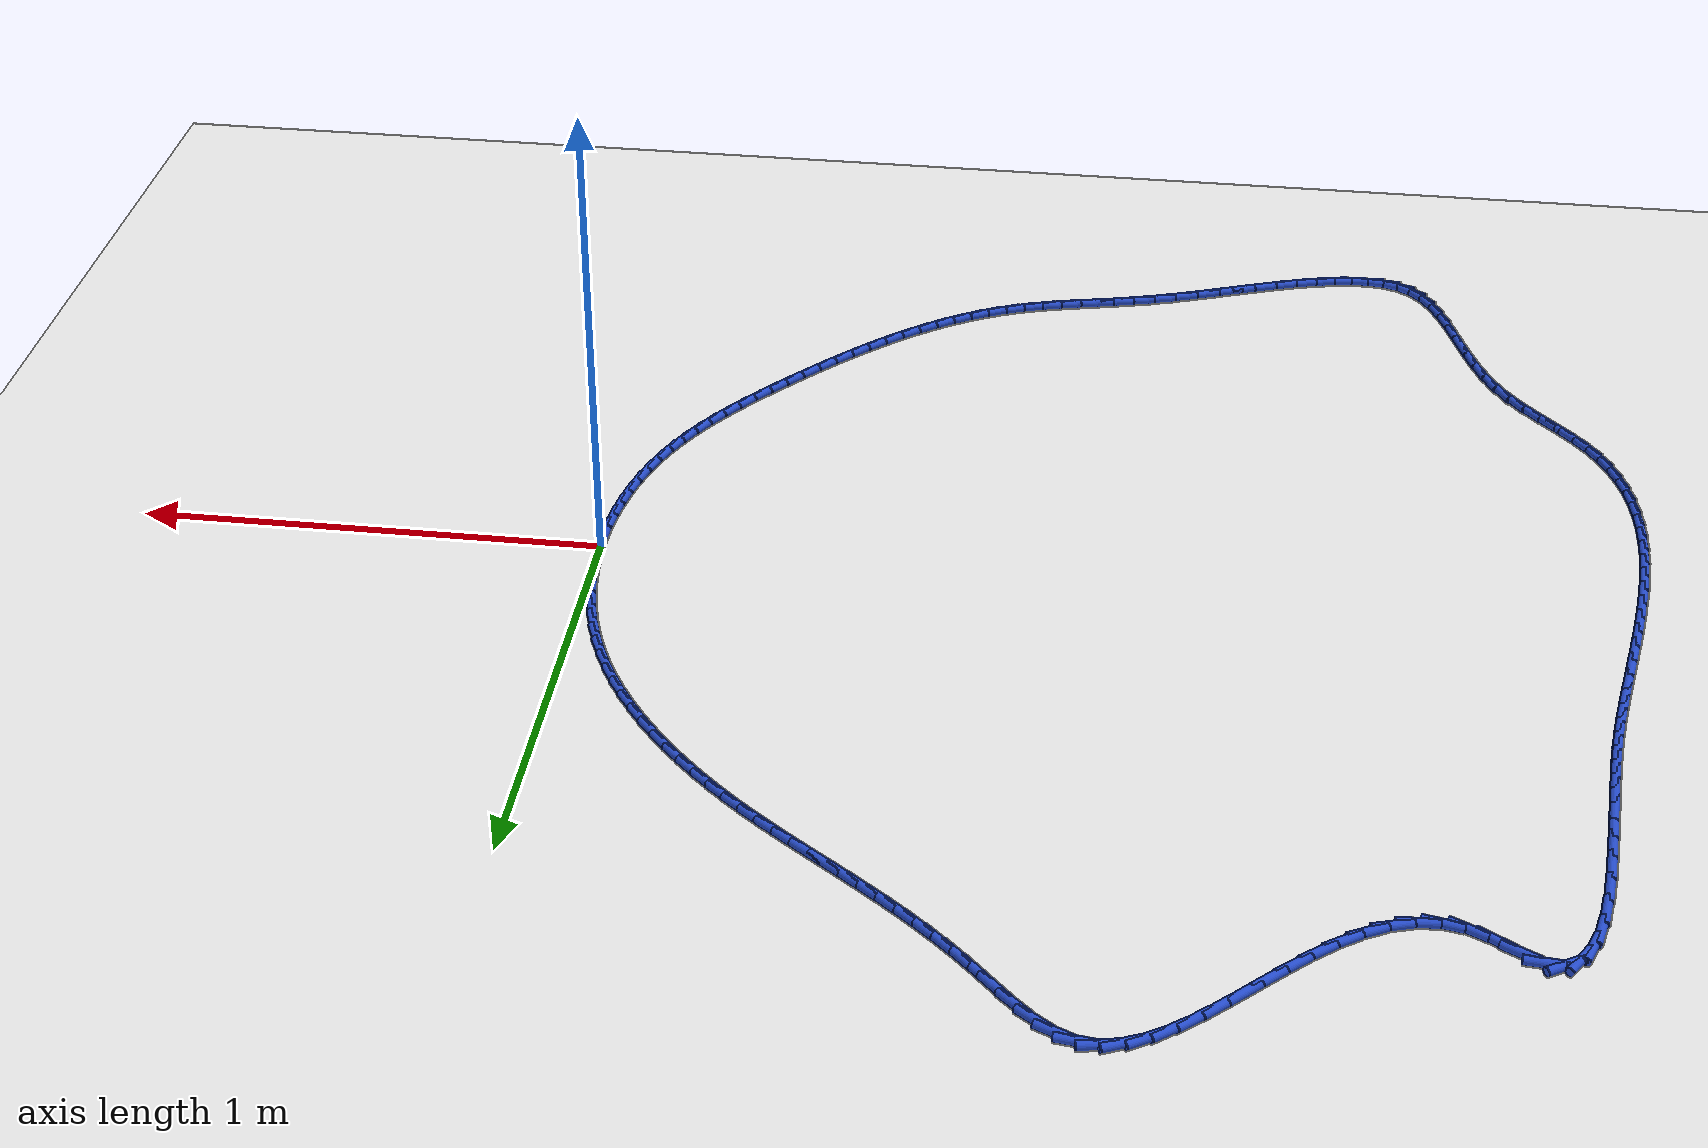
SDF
<sdf version="1.6">
 <world name="default">
  <light name="sun" type="directional">
   <pose>0 0 10 0 -0 0</pose>
   <diffuse>0.8 0.8 0.8 1</diffuse>
   <specular>0.2 0.2 0.2 1</specular>
   <attenuation>
    <range>1000</range>
    <constant>0.9</constant>
    <linear>0.01</linear>
    <quadratic>0.001</quadratic>
   </attenuation>
   <direction>-0.5 0.1 -0.9</direction>
  </light>
  <model name="ground_plane">
   <static>1</static>
   <link name="link">
    <collision name="collision">
     <geometry><plane><normal>0 0 1</normal><size>100 100</size></plane></geometry>
     <surface><friction><ode><mu>100</mu><mu2>50</mu2></ode></friction></surface>
    </collision>
    <visual name="visual">
     <cast_shadows>0</cast_shadows>
     <geometry><plane><normal>0 0 1</normal><size>100 100</size></plane></geometry>
     <material>
      <script><uri>file://media/materials/scripts/gazebo.material</uri><name>Gazebo/WhiteGlow</name></script>
     </material>
    </visual>
   </link>
  </model>
  <gravity>0 0 -9.8</gravity>
  <magnetic_field>6e-06 2.3e-05 -4.2e-05</magnetic_field>
  <atmosphere type="adiabatic"/>
  <physics name="default_physics" default="0" type="ode">
   <max_step_size>0.001</max_step_size>
   <real_time_factor>1</real_time_factor>
   <real_time_update_rate>1000</real_time_update_rate>
  </physics>
  <scene><ambient>0.4 0.4 0.4 1</ambient><background>0.7 0.7 0.7 1</background><shadows>1</shadows></scene>
  <spherical_coordinates>
   <surface_model>EARTH_WGS84</surface_model>
   <latitude_deg>0</latitude_deg>
   <longitude_deg>0</longitude_deg>
   <elevation>0</elevation>
   <heading_deg>0</heading_deg>
  </spherical_coordinates>
  <model name="line">
   <link name="link_0">
    <pose>1.3877787807814457e-17 6.938893903907228e-17 0.01 0 1.57 -1.5482072051248363</pose>
    <collision name="collision">
     <geometry><cylinder><radius>0.01</radius><length>0.08</length></cylinder></geometry>
    </collision>
    <visual name="visual">
     <material>
      <script><name>Gazebo/Blue</name><uri>file://media/materials/scripts/gazebo.material</uri></script>
     </material>
     <geometry><cylinder><radius>0.01</radius><length>0.08</length></cylinder></geometry>
    </visual>
   </link>
   <link name="link_1">
    <pose>-0.0010954406119171873 0.04848591718881564 0.01 0 1.57 -1.501787488764423</pose>
    <collision name="collision">
     <geometry><cylinder><radius>0.01</radius><length>0.08</length></cylinder></geometry>
    </collision>
    <visual name="visual">
     <material>
      <script><name>Gazebo/Blue</name><uri>file://media/materials/scripts/gazebo.material</uri></script>
     </material>
     <geometry><cylinder><radius>0.01</radius><length>0.08</length></cylinder></geometry>
    </visual>
   </link>
   <link name="link_2">
    <pose>-0.004433356410017526 0.09677850667080834 0.01 0 1.57 -1.4543632147195704</pose>
    <collision name="collision">
     <geometry><cylinder><radius>0.01</radius><length>0.08</length></cylinder></geometry>
    </collision>
    <visual name="visual">
     <material>
      <script><name>Gazebo/Blue</name><uri>file://media/materials/scripts/gazebo.material</uri></script>
     </material>
     <geometry><cylinder><radius>0.01</radius><length>0.08</length></cylinder></geometry>
    </visual>
   </link>
   <link name="link_3">
    <pose>-0.010046095050334335 0.14476616448148594 0.01 0 1.57 -1.4058237800581286</pose>
    <collision name="collision">
     <geometry><cylinder><radius>0.01</radius><length>0.08</length></cylinder></geometry>
    </collision>
    <visual name="visual">
     <material>
      <script><name>Gazebo/Blue</name><uri>file://media/materials/scripts/gazebo.material</uri></script>
     </material>
     <geometry><cylinder><radius>0.01</radius><length>0.08</length></cylinder></geometry>
    </visual>
   </link>
   <link name="link_4">
    <pose>-0.017966004188900972 0.19233728665635616 0.01 0 1.57 -1.3560721611729443</pose>
    <collision name="collision">
     <geometry><cylinder><radius>0.01</radius><length>0.08</length></cylinder></geometry>
    </collision>
    <visual name="visual">
     <material>
      <script><name>Gazebo/Blue</name><uri>file://media/materials/scripts/gazebo.material</uri></script>
     </material>
     <geometry><cylinder><radius>0.01</radius><length>0.08</length></cylinder></geometry>
    </visual>
   </link>
   <link name="link_5">
    <pose>-0.02822543148175078 0.2393802692309269 0.01 0 1.57 -1.3050284625541118</pose>
    <collision name="collision">
     <geometry><cylinder><radius>0.01</radius><length>0.08</length></cylinder></geometry>
    </collision>
    <visual name="visual">
     <material>
      <script><name>Gazebo/Blue</name><uri>file://media/materials/scripts/gazebo.material</uri></script>
     </material>
     <geometry><cylinder><radius>0.01</radius><length>0.08</length></cylinder></geometry>
    </visual>
   </link>
   <link name="link_6">
    <pose>-0.04085672458491714 0.285783508240706 0.01 0 1.57 -1.2526339373679325</pose>
    <collision name="collision">
     <geometry><cylinder><radius>0.01</radius><length>0.08</length></cylinder></geometry>
    </collision>
    <visual name="visual">
     <material>
      <script><name>Gazebo/Blue</name><uri>file://media/materials/scripts/gazebo.material</uri></script>
     </material>
     <geometry><cylinder><radius>0.01</radius><length>0.08</length></cylinder></geometry>
    </visual>
   </link>
   <link name="link_7">
    <pose>-0.05589223115443333 0.33143539972120095 0.01 0 1.57 -1.198855352976733</pose>
    <collision name="collision">
     <geometry><cylinder><radius>0.01</radius><length>0.08</length></cylinder></geometry>
    </collision>
    <visual name="visual">
     <material>
      <script><name>Gazebo/Blue</name><uri>file://media/materials/scripts/gazebo.material</uri></script>
     </material>
     <geometry><cylinder><radius>0.01</radius><length>0.08</length></cylinder></geometry>
    </visual>
   </link>
   <link name="link_8">
    <pose>-0.07336429884633273 0.3762243397079197 0.01 0 1.57 -1.1441724733756722</pose>
    <collision name="collision">
     <geometry><cylinder><radius>0.01</radius><length>0.08</length></cylinder></geometry>
    </collision>
    <visual name="visual">
     <material>
      <script><name>Gazebo/Blue</name><uri>file://media/materials/scripts/gazebo.material</uri></script>
     </material>
     <geometry><cylinder><radius>0.01</radius><length>0.08</length></cylinder></geometry>
    </visual>
   </link>
   <link name="link_9">
    <pose>-0.0932835645288864 0.42004714761470185 0.01 0 1.57 -1.091595191402601</pose>
    <collision name="collision">
     <geometry><cylinder><radius>0.01</radius><length>0.08</length></cylinder></geometry>
    </collision>
    <visual name="visual">
     <material>
      <script><name>Gazebo/Blue</name><uri>file://media/materials/scripts/gazebo.material</uri></script>
     </material>
     <geometry><cylinder><radius>0.01</radius><length>0.08</length></cylinder></geometry>
    </visual>
   </link>
   <link name="link_10">
    <pose>-0.11552537760816552 0.46285313185256727 0.01 0 1.57 -1.0422132514952542</pose>
    <collision name="collision">
     <geometry><cylinder><radius>0.01</radius><length>0.08</length></cylinder></geometry>
    </collision>
    <visual name="visual">
     <material>
      <script><name>Gazebo/Blue</name><uri>file://media/materials/scripts/gazebo.material</uri></script>
     </material>
     <geometry><cylinder><radius>0.01</radius><length>0.08</length></cylinder></geometry>
    </visual>
   </link>
   <link name="link_11">
    <pose>-0.1399130666953582 0.5046117839249792 0.01 0 1.57 -0.9959046782068822</pose>
    <collision name="collision">
     <geometry><cylinder><radius>0.01</radius><length>0.08</length></cylinder></geometry>
    </collision>
    <visual name="visual">
     <material>
      <script><name>Gazebo/Blue</name><uri>file://media/materials/scripts/gazebo.material</uri></script>
     </material>
     <geometry><cylinder><radius>0.01</radius><length>0.08</length></cylinder></geometry>
    </visual>
   </link>
   <link name="link_12">
    <pose>-0.16626985199106573 0.5452926373966743 0.01 0 1.57 -0.9525078751169277</pose>
    <collision name="collision">
     <geometry><cylinder><radius>0.01</radius><length>0.08</length></cylinder></geometry>
    </collision>
    <visual name="visual">
     <material>
      <script><name>Gazebo/Blue</name><uri>file://media/materials/scripts/gazebo.material</uri></script>
     </material>
     <geometry><cylinder><radius>0.01</radius><length>0.08</length></cylinder></geometry>
    </visual>
   </link>
   <link name="link_13">
    <pose>-0.1944189536958893 0.5848652258323891 0.01 0 1.57 -0.911837483212894</pose>
    <collision name="collision">
     <geometry><cylinder><radius>0.01</radius><length>0.08</length></cylinder></geometry>
    </collision>
    <visual name="visual">
     <material>
      <script><name>Gazebo/Blue</name><uri>file://media/materials/scripts/gazebo.material</uri></script>
     </material>
     <geometry><cylinder><radius>0.01</radius><length>0.08</length></cylinder></geometry>
    </visual>
   </link>
   <link name="link_14">
    <pose>-0.22418359201043045 0.6232990827968604 0.01 0 1.57 -0.8736948732035715</pose>
    <collision name="collision">
     <geometry><cylinder><radius>0.01</radius><length>0.08</length></cylinder></geometry>
    </collision>
    <visual name="visual">
     <material>
      <script><name>Gazebo/Blue</name><uri>file://media/materials/scripts/gazebo.material</uri></script>
     </material>
     <geometry><cylinder><radius>0.01</radius><length>0.08</length></cylinder></geometry>
    </visual>
   </link>
   <link name="link_15">
    <pose>-0.25538698713529034 0.6605637418548251 0.01 0 1.57 -0.8378758866540472</pose>
    <collision name="collision">
     <geometry><cylinder><radius>0.01</radius><length>0.08</length></cylinder></geometry>
    </collision>
    <visual name="visual">
     <material>
      <script><name>Gazebo/Blue</name><uri>file://media/materials/scripts/gazebo.material</uri></script>
     </material>
     <geometry><cylinder><radius>0.01</radius><length>0.08</length></cylinder></geometry>
    </visual>
   </link>
   <link name="link_16">
    <pose>-0.28785235927107045 0.69662873657102 0.01 0 1.57 -0.8041761921825845</pose>
    <collision name="collision">
     <geometry><cylinder><radius>0.01</radius><length>0.08</length></cylinder></geometry>
    </collision>
    <visual name="visual">
     <material>
      <script><name>Gazebo/Blue</name><uri>file://media/materials/scripts/gazebo.material</uri></script>
     </material>
     <geometry><cylinder><radius>0.01</radius><length>0.08</length></cylinder></geometry>
    </visual>
   </link>
   <link name="link_17">
    <pose>-0.321402928618372 0.7314636005101814 0.01 0 1.57 -0.7723946670096957</pose>
    <collision name="collision">
     <geometry><cylinder><radius>0.01</radius><length>0.08</length></cylinder></geometry>
    </collision>
    <visual name="visual">
     <material>
      <script><name>Gazebo/Blue</name><uri>file://media/materials/scripts/gazebo.material</uri></script>
     </material>
     <geometry><cylinder><radius>0.01</radius><length>0.08</length></cylinder></geometry>
    </visual>
   </link>
   <link name="link_18">
    <pose>-0.3558619153777963 0.7650378672370467 0.01 0 1.57 -0.7423351864331231</pose>
    <collision name="collision">
     <geometry><cylinder><radius>0.01</radius><length>0.08</length></cylinder></geometry>
    </collision>
    <visual name="visual">
     <material>
      <script><name>Gazebo/Blue</name><uri>file://media/materials/scripts/gazebo.material</uri></script>
     </material>
     <geometry><cylinder><radius>0.01</radius><length>0.08</length></cylinder></geometry>
    </visual>
   </link>
   <link name="link_19">
    <pose>-0.3910525397499448 0.7973210703163522 0.01 0 1.57 -0.7138536059161544</pose>
    <collision name="collision">
     <geometry><cylinder><radius>0.01</radius><length>0.08</length></cylinder></geometry>
    </collision>
    <visual name="visual">
     <material>
      <script><name>Gazebo/Blue</name><uri>file://media/materials/scripts/gazebo.material</uri></script>
     </material>
     <geometry><cylinder><radius>0.01</radius><length>0.08</length></cylinder></geometry>
    </visual>
   </link>
   <link name="link_20">
    <pose>-0.42679973112854386 0.8282871311962707 0.01 0 1.57 -0.6883064348828172</pose>
    <collision name="collision">
     <geometry><cylinder><radius>0.01</radius><length>0.08</length></cylinder></geometry>
    </collision>
    <visual name="visual">
     <material>
      <script><name>Gazebo/Blue</name><uri>file://media/materials/scripts/gazebo.material</uri></script>
     </material>
     <geometry><cylinder><radius>0.01</radius><length>0.08</length></cylinder></geometry>
    </visual>
   </link>
   <link name="link_21">
    <pose>-0.4629815781682702 0.858046443112251 0.01 0 1.57 -0.6676496734134616</pose>
    <collision name="collision">
     <geometry><cylinder><radius>0.01</radius><length>0.08</length></cylinder></geometry>
    </collision>
    <visual name="visual">
     <material>
      <script><name>Gazebo/Blue</name><uri>file://media/materials/scripts/gazebo.material</uri></script>
     </material>
     <geometry><cylinder><radius>0.01</radius><length>0.08</length></cylinder></geometry>
    </visual>
   </link>
   <link name="link_22">
    <pose>-0.49953839362850516 0.8868691425811355 0.01 0 1.57 -0.6522695162933421</pose>
    <collision name="collision">
     <geometry><cylinder><radius>0.01</radius><length>0.08</length></cylinder></geometry>
    </collision>
    <visual name="visual">
     <material>
      <script><name>Gazebo/Blue</name><uri>file://media/materials/scripts/gazebo.material</uri></script>
     </material>
     <geometry><cylinder><radius>0.01</radius><length>0.08</length></cylinder></geometry>
    </visual>
   </link>
   <link name="link_23">
    <pose>-0.5364140265312488 0.9150344445018078 0.01 0 1.57 -0.6423523197538931</pose>
    <collision name="collision">
     <geometry><cylinder><radius>0.01</radius><length>0.08</length></cylinder></geometry>
    </collision>
    <visual name="visual">
     <material>
      <script><name>Gazebo/Blue</name><uri>file://media/materials/scripts/gazebo.material</uri></script>
     </material>
     <geometry><cylinder><radius>0.01</radius><length>0.08</length></cylinder></geometry>
    </visual>
   </link>
   <link name="link_24">
    <pose>-0.5735523258985015 0.9428215637731512 0.01 0 1.57 -0.6379865458825893</pose>
    <collision name="collision">
     <geometry><cylinder><radius>0.01</radius><length>0.08</length></cylinder></geometry>
    </collision>
    <visual name="visual">
     <material>
      <script><name>Gazebo/Blue</name><uri>file://media/materials/scripts/gazebo.material</uri></script>
     </material>
     <geometry><cylinder><radius>0.01</radius><length>0.08</length></cylinder></geometry>
    </visual>
   </link>
   <link name="link_25">
    <pose>-0.6108971407522635 0.9705097152940492 0.01 0 1.57 -0.6391689251276169</pose>
    <collision name="collision">
     <geometry><cylinder><radius>0.01</radius><length>0.08</length></cylinder></geometry>
    </collision>
    <visual name="visual">
     <material>
      <script><name>Gazebo/Blue</name><uri>file://media/materials/scripts/gazebo.material</uri></script>
     </material>
     <geometry><cylinder><radius>0.01</radius><length>0.08</length></cylinder></geometry>
    </visual>
   </link>
   <link name="link_26">
    <pose>-0.6483923201145351 0.9983781139633847 0.01 0 1.57 -0.6458095160340973</pose>
    <collision name="collision">
     <geometry><cylinder><radius>0.01</radius><length>0.08</length></cylinder></geometry>
    </collision>
    <visual name="visual">
     <material>
      <script><name>Gazebo/Blue</name><uri>file://media/materials/scripts/gazebo.material</uri></script>
     </material>
     <geometry><cylinder><radius>0.01</radius><length>0.08</length></cylinder></geometry>
    </visual>
   </link>
   <link name="link_27">
    <pose>-0.6859817130073167 1.0267059746800418 0.01 0 1.57 -0.657735107498253</pose>
    <collision name="collision">
     <geometry><cylinder><radius>0.01</radius><length>0.08</length></cylinder></geometry>
    </collision>
    <visual name="visual">
     <material>
      <script><name>Gazebo/Blue</name><uri>file://media/materials/scripts/gazebo.material</uri></script>
     </material>
     <geometry><cylinder><radius>0.01</radius><length>0.08</length></cylinder></geometry>
    </visual>
   </link>
   <link name="link_28">
    <pose>-0.7236091684526085 1.0557725123429034 0.01 0 1.57 -0.6746912622402574</pose>
    <collision name="collision">
     <geometry><cylinder><radius>0.01</radius><length>0.08</length></cylinder></geometry>
    </collision>
    <visual name="visual">
     <material>
      <script><name>Gazebo/Blue</name><uri>file://media/materials/scripts/gazebo.material</uri></script>
     </material>
     <geometry><cylinder><radius>0.01</radius><length>0.08</length></cylinder></geometry>
    </visual>
   </link>
   <link name="link_29">
    <pose>-0.7612185354724107 1.085856941850853 0.01 0 1.57 -0.6963440058009722</pose>
    <collision name="collision">
     <geometry><cylinder><radius>0.01</radius><length>0.08</length></cylinder></geometry>
    </collision>
    <visual name="visual">
     <material>
      <script><name>Gazebo/Blue</name><uri>file://media/materials/scripts/gazebo.material</uri></script>
     </material>
     <geometry><cylinder><radius>0.01</radius><length>0.08</length></cylinder></geometry>
    </visual>
   </link>
   <link name="link_30">
    <pose>-0.7987536630887233 1.1172384781027738 0.01 0 1.57 -0.722282626750278</pose>
    <collision name="collision">
     <geometry><cylinder><radius>0.01</radius><length>0.08</length></cylinder></geometry>
    </collision>
    <visual name="visual">
     <material>
      <script><name>Gazebo/Blue</name><uri>file://media/materials/scripts/gazebo.material</uri></script>
     </material>
     <geometry><cylinder><radius>0.01</radius><length>0.08</length></cylinder></geometry>
    </visual>
   </link>
   <link name="link_31">
    <pose>-0.8361584003235474 1.1501963359975493 0.01 0 1.57 -0.7520251866921546</pose>
    <collision name="collision">
     <geometry><cylinder><radius>0.01</radius><length>0.08</length></cylinder></geometry>
    </collision>
    <visual name="visual">
     <material>
      <script><name>Gazebo/Blue</name><uri>file://media/materials/scripts/gazebo.material</uri></script>
     </material>
     <geometry><cylinder><radius>0.01</radius><length>0.08</length></cylinder></geometry>
    </visual>
   </link>
   <link name="link_32">
    <pose>-0.8733765961988829 1.185009730434063 0.01 0 1.57 -0.7850167899247315</pose>
    <collision name="collision">
     <geometry><cylinder><radius>0.01</radius><length>0.08</length></cylinder></geometry>
    </collision>
    <visual name="visual">
     <material>
      <script><name>Gazebo/Blue</name><uri>file://media/materials/scripts/gazebo.material</uri></script>
     </material>
     <geometry><cylinder><radius>0.01</radius><length>0.08</length></cylinder></geometry>
    </visual>
   </link>
   <link name="link_33">
    <pose>-0.9103521577971397 1.2219570997860632 0.01 0 1.57 -0.8103170245100896</pose>
    <collision name="collision">
     <geometry><cylinder><radius>0.01</radius><length>0.08</length></cylinder></geometry>
    </collision>
    <visual name="visual">
     <material>
      <script><name>Gazebo/Blue</name><uri>file://media/materials/scripts/gazebo.material</uri></script>
     </material>
     <geometry><cylinder><radius>0.01</radius><length>0.08</length></cylinder></geometry>
    </visual>
   </link>
   <link name="link_34">
    <pose>-0.9470850002560282 1.260567806382027 0.01 0 1.57 -0.7989413287640867</pose>
    <collision name="collision">
     <geometry><cylinder><radius>0.01</radius><length>0.08</length></cylinder></geometry>
    </collision>
    <visual name="visual">
     <material>
      <script><name>Gazebo/Blue</name><uri>file://media/materials/scripts/gazebo.material</uri></script>
     </material>
     <geometry><cylinder><radius>0.01</radius><length>0.08</length></cylinder></geometry>
    </visual>
   </link>
   <link name="link_35">
    <pose>-0.9837355283522464 1.298224754448264 0.01 0 1.57 -0.7420945817457969</pose>
    <collision name="collision">
     <geometry><cylinder><radius>0.01</radius><length>0.08</length></cylinder></geometry>
    </collision>
    <visual name="visual">
     <material>
      <script><name>Gazebo/Blue</name><uri>file://media/materials/scripts/gazebo.material</uri></script>
     </material>
     <geometry><cylinder><radius>0.01</radius><length>0.08</length></cylinder></geometry>
    </visual>
   </link>
   <link name="link_36">
    <pose>-1.0204927120035454 1.3319288056142253 0.01 0 1.57 -0.6253369880694639</pose>
    <collision name="collision">
     <geometry><cylinder><radius>0.01</radius><length>0.08</length></cylinder></geometry>
    </collision>
    <visual name="visual">
     <material>
      <script><name>Gazebo/Blue</name><uri>file://media/materials/scripts/gazebo.material</uri></script>
     </material>
     <geometry><cylinder><radius>0.01</radius><length>0.08</length></cylinder></geometry>
    </visual>
   </link>
   <link name="link_37">
    <pose>-1.0575455211276743 1.3586808215093604 0.01 0 1.57 -0.42083631800951915</pose>
    <collision name="collision">
     <geometry><cylinder><radius>0.01</radius><length>0.08</length></cylinder></geometry>
    </collision>
    <visual name="visual">
     <material>
      <script><name>Gazebo/Blue</name><uri>file://media/materials/scripts/gazebo.material</uri></script>
     </material>
     <geometry><cylinder><radius>0.01</radius><length>0.08</length></cylinder></geometry>
    </visual>
   </link>
   <link name="link_38">
    <pose>-1.095082925642384 1.3754816637631182 0.01 0 1.57 -0.11529514805836497</pose>
    <collision name="collision">
     <geometry><cylinder><radius>0.01</radius><length>0.08</length></cylinder></geometry>
    </collision>
    <visual name="visual">
     <material>
      <script><name>Gazebo/Blue</name><uri>file://media/materials/scripts/gazebo.material</uri></script>
     </material>
     <geometry><cylinder><radius>0.01</radius><length>0.08</length></cylinder></geometry>
    </visual>
   </link>
   <link name="link_39">
    <pose>-1.1332672386760871 1.3799037413575044 0.01 0 1.57 0.18537166887914516</pose>
    <collision name="collision">
     <geometry><cylinder><radius>0.01</radius><length>0.08</length></cylinder></geometry>
    </collision>
    <visual name="visual">
     <material>
      <script><name>Gazebo/Blue</name><uri>file://media/materials/scripts/gazebo.material</uri></script>
     </material>
     <geometry><cylinder><radius>0.01</radius><length>0.08</length></cylinder></geometry>
    </visual>
   </link>
   <link name="link_40">
    <pose>-1.172116230520439 1.3726186015328443 0.01 0 1.57 0.41244498337102103</pose>
    <collision name="collision">
     <geometry><cylinder><radius>0.01</radius><length>0.08</length></cylinder></geometry>
    </collision>
    <visual name="visual">
     <material>
      <script><name>Gazebo/Blue</name><uri>file://media/materials/scripts/gazebo.material</uri></script>
     </material>
     <geometry><cylinder><radius>0.01</radius><length>0.08</length></cylinder></geometry>
    </visual>
   </link>
   <link name="link_41">
    <pose>-1.2115989090555994 1.3553433048072339 0.01 0 1.57 0.5674167489670434</pose>
    <collision name="collision">
     <geometry><cylinder><radius>0.01</radius><length>0.08</length></cylinder></geometry>
    </collision>
    <visual name="visual">
     <material>
      <script><name>Gazebo/Blue</name><uri>file://media/materials/scripts/gazebo.material</uri></script>
     </material>
     <geometry><cylinder><radius>0.01</radius><length>0.08</length></cylinder></geometry>
    </visual>
   </link>
   <link name="link_42">
    <pose>-1.2516842445835892 1.3297957174104007 0.01 0 1.57 0.6683562304352626</pose>
    <collision name="collision">
     <geometry><cylinder><radius>0.01</radius><length>0.08</length></cylinder></geometry>
    </collision>
    <visual name="visual">
     <material>
      <script><name>Gazebo/Blue</name><uri>file://media/materials/scripts/gazebo.material</uri></script>
     </material>
     <geometry><cylinder><radius>0.01</radius><length>0.08</length></cylinder></geometry>
    </visual>
   </link>
   <link name="link_43">
    <pose>-1.2923412074064307 1.2976937055720725 0.01 0 1.57 0.7309447375592028</pose>
    <collision name="collision">
     <geometry><cylinder><radius>0.01</radius><length>0.08</length></cylinder></geometry>
    </collision>
    <visual name="visual">
     <material>
      <script><name>Gazebo/Blue</name><uri>file://media/materials/scripts/gazebo.material</uri></script>
     </material>
     <geometry><cylinder><radius>0.01</radius><length>0.08</length></cylinder></geometry>
    </visual>
   </link>
   <link name="link_44">
    <pose>-1.3335387678261452 1.2607551355219766 0.01 0 1.57 0.765222602714156</pose>
    <collision name="collision">
     <geometry><cylinder><radius>0.01</radius><length>0.08</length></cylinder></geometry>
    </collision>
    <visual name="visual">
     <material>
      <script><name>Gazebo/Blue</name><uri>file://media/materials/scripts/gazebo.material</uri></script>
     </material>
     <geometry><cylinder><radius>0.01</radius><length>0.08</length></cylinder></geometry>
    </visual>
   </link>
   <link name="link_45">
    <pose>-1.3752458961447538 1.220697873489841 0.01 0 1.57 0.7766998404765895</pose>
    <collision name="collision">
     <geometry><cylinder><radius>0.01</radius><length>0.08</length></cylinder></geometry>
    </collision>
    <visual name="visual">
     <material>
      <script><name>Gazebo/Blue</name><uri>file://media/materials/scripts/gazebo.material</uri></script>
     </material>
     <geometry><cylinder><radius>0.01</radius><length>0.08</length></cylinder></geometry>
    </visual>
   </link>
   <link name="link_46">
    <pose>-1.4174315626642782 1.1792397857053931 0.01 0 1.57 0.7675887476218077</pose>
    <collision name="collision">
     <geometry><cylinder><radius>0.01</radius><length>0.08</length></cylinder></geometry>
    </collision>
    <visual name="visual">
     <material>
      <script><name>Gazebo/Blue</name><uri>file://media/materials/scripts/gazebo.material</uri></script>
     </material>
     <geometry><cylinder><radius>0.01</radius><length>0.08</length></cylinder></geometry>
    </visual>
   </link>
   <link name="link_47">
    <pose>-1.46006473768674 1.1380987383983612 0.01 0 1.57 0.7374345503258862</pose>
    <collision name="collision">
     <geometry><cylinder><radius>0.01</radius><length>0.08</length></cylinder></geometry>
    </collision>
    <visual name="visual">
     <material>
      <script><name>Gazebo/Blue</name><uri>file://media/materials/scripts/gazebo.material</uri></script>
     </material>
     <geometry><cylinder><radius>0.01</radius><length>0.08</length></cylinder></geometry>
    </visual>
   </link>
   <link name="link_48">
    <pose>-1.5031143915141605 1.0989925977984718 0.01 0 1.57 0.6831805620847076</pose>
    <collision name="collision">
     <geometry><cylinder><radius>0.01</radius><length>0.08</length></cylinder></geometry>
    </collision>
    <visual name="visual">
     <material>
      <script><name>Gazebo/Blue</name><uri>file://media/materials/scripts/gazebo.material</uri></script>
     </material>
     <geometry><cylinder><radius>0.01</radius><length>0.08</length></cylinder></geometry>
    </visual>
   </link>
   <link name="link_49">
    <pose>-1.5465494944485612 1.0636392301354538 0.01 0 1.57 0.5988277823123604</pose>
    <collision name="collision">
     <geometry><cylinder><radius>0.01</radius><length>0.08</length></cylinder></geometry>
    </collision>
    <visual name="visual">
     <material>
      <script><name>Gazebo/Blue</name><uri>file://media/materials/scripts/gazebo.material</uri></script>
     </material>
     <geometry><cylinder><radius>0.01</radius><length>0.08</length></cylinder></geometry>
    </visual>
   </link>
   <link name="link_50">
    <pose>-1.5903390167919635 1.0337565016390338 0.01 0 1.57 0.47514668384444686</pose>
    <collision name="collision">
     <geometry><cylinder><radius>0.01</radius><length>0.08</length></cylinder></geometry>
    </collision>
    <visual name="visual">
     <material>
      <script><name>Gazebo/Blue</name><uri>file://media/materials/scripts/gazebo.material</uri></script>
     </material>
     <geometry><cylinder><radius>0.01</radius><length>0.08</length></cylinder></geometry>
    </visual>
   </link>
   <link name="link_51">
    <pose>-1.6344519288463895 1.01106227853894 0.01 0 1.57 0.30106206603726887</pose>
    <collision name="collision">
     <geometry><cylinder><radius>0.01</radius><length>0.08</length></cylinder></geometry>
    </collision>
    <visual name="visual">
     <material>
      <script><name>Gazebo/Blue</name><uri>file://media/materials/scripts/gazebo.material</uri></script>
     </material>
     <geometry><cylinder><radius>0.01</radius><length>0.08</length></cylinder></geometry>
    </visual>
   </link>
   <link name="link_52">
    <pose>-1.6788572009138591 0.9972744270648999 0.01 0 1.57 0.07070919263407373</pose>
    <collision name="collision">
     <geometry><cylinder><radius>0.01</radius><length>0.08</length></cylinder></geometry>
    </collision>
    <visual name="visual">
     <material>
      <script><name>Gazebo/Blue</name><uri>file://media/materials/scripts/gazebo.material</uri></script>
     </material>
     <geometry><cylinder><radius>0.01</radius><length>0.08</length></cylinder></geometry>
    </visual>
   </link>
   <link name="link_53">
    <pose>-1.7235238032963967 0.9941108134466412 0.01 0 1.57 -0.2016561543358557</pose>
    <collision name="collision">
     <geometry><cylinder><radius>0.01</radius><length>0.08</length></cylinder></geometry>
    </collision>
    <visual name="visual">
     <material>
      <script><name>Gazebo/Blue</name><uri>file://media/materials/scripts/gazebo.material</uri></script>
     </material>
     <geometry><cylinder><radius>0.01</radius><length>0.08</length></cylinder></geometry>
    </visual>
   </link>
   <link name="link_54">
    <pose>-1.7684207062960207 1.0032893039138915 0.01 0 1.57 -0.46210928625707387</pose>
    <collision name="collision">
     <geometry><cylinder><radius>0.01</radius><length>0.08</length></cylinder></geometry>
    </collision>
    <visual name="visual">
     <material>
      <script><name>Gazebo/Blue</name><uri>file://media/materials/scripts/gazebo.material</uri></script>
     </material>
     <geometry><cylinder><radius>0.01</radius><length>0.08</length></cylinder></geometry>
    </visual>
   </link>
   <link name="link_55">
    <pose>-1.8133858660015767 1.0256854864921512 0.01 0 1.57 -0.5722259225936407</pose>
    <collision name="collision">
     <geometry><cylinder><radius>0.01</radius><length>0.08</length></cylinder></geometry>
    </collision>
    <visual name="visual">
     <material>
      <script><name>Gazebo/Blue</name><uri>file://media/materials/scripts/gazebo.material</uri></script>
     </material>
     <geometry><cylinder><radius>0.01</radius><length>0.08</length></cylinder></geometry>
    </visual>
   </link>
   <link name="link_56">
    <pose>-1.8569456606068853 1.0537429367760447 0.01 0 1.57 -0.490184879598049</pose>
    <collision name="collision">
     <geometry><cylinder><radius>0.01</radius><length>0.08</length></cylinder></geometry>
    </collision>
    <visual name="visual">
     <material>
      <script><name>Gazebo/Blue</name><uri>file://media/materials/scripts/gazebo.material</uri></script>
     </material>
     <geometry><cylinder><radius>0.01</radius><length>0.08</length></cylinder></geometry>
    </visual>
   </link>
   <link name="link_57">
    <pose>-1.8968709537066084 1.0750480971956689 0.01 0 1.57 -0.08659081036548558</pose>
    <collision name="collision">
     <geometry><cylinder><radius>0.01</radius><length>0.08</length></cylinder></geometry>
    </collision>
    <visual name="visual">
     <material>
      <script><name>Gazebo/Blue</name><uri>file://media/materials/scripts/gazebo.material</uri></script>
     </material>
     <geometry><cylinder><radius>0.01</radius><length>0.08</length></cylinder></geometry>
    </visual>
   </link>
   <link name="link_58">
    <pose>-1.9310862112329228 1.0780182511586278 0.01 0 1.57 0.5546874246644931</pose>
    <collision name="collision">
     <geometry><cylinder><radius>0.01</radius><length>0.08</length></cylinder></geometry>
    </collision>
    <visual name="visual">
     <material>
      <script><name>Gazebo/Blue</name><uri>file://media/materials/scripts/gazebo.material</uri></script>
     </material>
     <geometry><cylinder><radius>0.01</radius><length>0.08</length></cylinder></geometry>
    </visual>
   </link>
   <link name="link_59">
    <pose>-1.9592532047016973 1.0605667349842203 0.01 0 1.57 0.982280465411509</pose>
    <collision name="collision">
     <geometry><cylinder><radius>0.01</radius><length>0.08</length></cylinder></geometry>
    </collision>
    <visual name="visual">
     <material>
      <script><name>Gazebo/Blue</name><uri>file://media/materials/scripts/gazebo.material</uri></script>
     </material>
     <geometry><cylinder><radius>0.01</radius><length>0.08</length></cylinder></geometry>
    </visual>
   </link>
   <link name="link_60">
    <pose>-1.982085556281319 1.0263562646894067 0.01 0 1.57 1.2024798161804648</pose>
    <collision name="collision">
     <geometry><cylinder><radius>0.01</radius><length>0.08</length></cylinder></geometry>
    </collision>
    <visual name="visual">
     <material>
      <script><name>Gazebo/Blue</name><uri>file://media/materials/scripts/gazebo.material</uri></script>
     </material>
     <geometry><cylinder><radius>0.01</radius><length>0.08</length></cylinder></geometry>
    </visual>
   </link>
   <link name="link_61">
    <pose>-2.0003115646295058 0.9791297774799423 0.01 0 1.57 1.3221051690939472</pose>
    <collision name="collision">
     <geometry><cylinder><radius>0.01</radius><length>0.08</length></cylinder></geometry>
    </collision>
    <visual name="visual">
     <material>
      <script><name>Gazebo/Blue</name><uri>file://media/materials/scripts/gazebo.material</uri></script>
     </material>
     <geometry><cylinder><radius>0.01</radius><length>0.08</length></cylinder></geometry>
    </visual>
   </link>
   <link name="link_62">
    <pose>-2.014659528403973 0.9226302105615845 0.01 0 1.57 1.392190156301244</pose>
    <collision name="collision">
     <geometry><cylinder><radius>0.01</radius><length>0.08</length></cylinder></geometry>
    </collision>
    <visual name="visual">
     <material>
      <script><name>Gazebo/Blue</name><uri>file://media/materials/scripts/gazebo.material</uri></script>
     </material>
     <geometry><cylinder><radius>0.01</radius><length>0.08</length></cylinder></geometry>
    </visual>
   </link>
   <link name="link_63">
    <pose>-2.025857746262438 0.8606005011400883 0.01 0 1.57 1.4341232548136582</pose>
    <collision name="collision">
     <geometry><cylinder><radius>0.01</radius><length>0.08</length></cylinder></geometry>
    </collision>
    <visual name="visual">
     <material>
      <script><name>Gazebo/Blue</name><uri>file://media/materials/scripts/gazebo.material</uri></script>
     </material>
     <geometry><cylinder><radius>0.01</radius><length>0.08</length></cylinder></geometry>
    </visual>
   </link>
   <link name="link_64">
    <pose>-2.034634516862617 0.7967835864212114 0.01 0 1.57 1.4567845629368146</pose>
    <collision name="collision">
     <geometry><cylinder><radius>0.01</radius><length>0.08</length></cylinder></geometry>
    </collision>
    <visual name="visual">
     <material>
      <script><name>Gazebo/Blue</name><uri>file://media/materials/scripts/gazebo.material</uri></script>
     </material>
     <geometry><cylinder><radius>0.01</radius><length>0.08</length></cylinder></geometry>
    </visual>
   </link>
   <link name="link_65">
    <pose>-2.04171813876377 0.7349224025535356 0.01 0 1.57 1.4651222404747108</pose>
    <collision name="collision">
     <geometry><cylinder><radius>0.01</radius><length>0.08</length></cylinder></geometry>
    </collision>
    <visual name="visual">
     <material>
      <script><name>Gazebo/Blue</name><uri>file://media/materials/scripts/gazebo.material</uri></script>
     </material>
     <geometry><cylinder><radius>0.01</radius><length>0.08</length></cylinder></geometry>
    </visual>
   </link>
   <link name="link_66">
    <pose>-2.0477613309545806 0.6779483530487364 0.01 0 1.57 1.4686022576897921</pose>
    <collision name="collision">
     <geometry><cylinder><radius>0.01</radius><length>0.08</length></cylinder></geometry>
    </collision>
    <visual name="visual">
     <material>
      <script><name>Gazebo/Blue</name><uri>file://media/materials/scripts/gazebo.material</uri></script>
     </material>
     <geometry><cylinder><radius>0.01</radius><length>0.08</length></cylinder></geometry>
    </visual>
   </link>
   <link name="link_67">
    <pose>-2.0531243432750554 0.6256524655521167 0.01 0 1.57 1.4688106715112843</pose>
    <collision name="collision">
     <geometry><cylinder><radius>0.01</radius><length>0.08</length></cylinder></geometry>
    </collision>
    <visual name="visual">
     <material>
      <script><name>Gazebo/Blue</name><uri>file://media/materials/scripts/gazebo.material</uri></script>
     </material>
     <geometry><cylinder><radius>0.01</radius><length>0.08</length></cylinder></geometry>
    </visual>
   </link>
   <link name="link_68">
    <pose>-2.058096690854146 0.5770662565587024 0.01 0 1.57 1.464939897385308</pose>
    <collision name="collision">
     <geometry><cylinder><radius>0.01</radius><length>0.08</length></cylinder></geometry>
    </collision>
    <visual name="visual">
     <material>
      <script><name>Gazebo/Blue</name><uri>file://media/materials/scripts/gazebo.material</uri></script>
     </material>
     <geometry><cylinder><radius>0.01</radius><length>0.08</length></cylinder></geometry>
    </visual>
   </link>
   <link name="link_69">
    <pose>-2.0629678888208005 0.5312212425635199 0.01 0 1.57 1.4564952796618205</pose>
    <collision name="collision">
     <geometry><cylinder><radius>0.01</radius><length>0.08</length></cylinder></geometry>
    </collision>
    <visual name="visual">
     <material>
      <script><name>Gazebo/Blue</name><uri>file://media/materials/scripts/gazebo.material</uri></script>
     </material>
     <geometry><cylinder><radius>0.01</radius><length>0.08</length></cylinder></geometry>
    </visual>
   </link>
   <link name="link_70">
    <pose>-2.0680274523039683 0.48714894006159476 0.01 0 1.57 1.4435083546158418</pose>
    <collision name="collision">
     <geometry><cylinder><radius>0.01</radius><length>0.08</length></cylinder></geometry>
    </collision>
    <visual name="visual">
     <material>
      <script><name>Gazebo/Blue</name><uri>file://media/materials/scripts/gazebo.material</uri></script>
     </material>
     <geometry><cylinder><radius>0.01</radius><length>0.08</length></cylinder></geometry>
    </visual>
   </link>
   <link name="link_71">
    <pose>-2.0735648964326003 0.44388086554795286 0.01 0 1.57 1.4266386286954926</pose>
    <collision name="collision">
     <geometry><cylinder><radius>0.01</radius><length>0.08</length></cylinder></geometry>
    </collision>
    <visual name="visual">
     <material>
      <script><name>Gazebo/Blue</name><uri>file://media/materials/scripts/gazebo.material</uri></script>
     </material>
     <geometry><cylinder><radius>0.01</radius><length>0.08</length></cylinder></geometry>
    </visual>
   </link>
   <link name="link_72">
    <pose>-2.0798697363356435 0.4004485355176209 0.01 0 1.57 1.407288552375491</pose>
    <collision name="collision">
     <geometry><cylinder><radius>0.01</radius><length>0.08</length></cylinder></geometry>
    </collision>
    <visual name="visual">
     <material>
      <script><name>Gazebo/Blue</name><uri>file://media/materials/scripts/gazebo.material</uri></script>
     </material>
     <geometry><cylinder><radius>0.01</radius><length>0.08</length></cylinder></geometry>
    </visual>
   </link>
   <link name="link_73">
    <pose>-2.0872170738382554 0.3559139926407003 0.01 0 1.57 1.3903331808201964</pose>
    <collision name="collision">
     <geometry><cylinder><radius>0.01</radius><length>0.08</length></cylinder></geometry>
    </collision>
    <visual name="visual">
     <material>
      <script><name>Gazebo/Blue</name><uri>file://media/materials/scripts/gazebo.material</uri></script>
     </material>
     <geometry><cylinder><radius>0.01</radius><length>0.08</length></cylinder></geometry>
    </visual>
   </link>
   <link name="link_74">
    <pose>-2.095609074090091 0.3099173366975593 0.01 0 1.57 1.3788032745397638</pose>
    <collision name="collision">
     <geometry><cylinder><radius>0.01</radius><length>0.08</length></cylinder></geometry>
    </collision>
    <visual name="visual">
     <material>
      <script><name>Gazebo/Blue</name><uri>file://media/materials/scripts/gazebo.material</uri></script>
     </material>
     <geometry><cylinder><radius>0.01</radius><length>0.08</length></cylinder></geometry>
    </visual>
   </link>
   <link name="link_75">
    <pose>-2.1048040124326817 0.262615205736841 0.01 0 1.57 1.3721897861753036</pose>
    <collision name="collision">
     <geometry><cylinder><radius>0.01</radius><length>0.08</length></cylinder></geometry>
    </collision>
    <visual name="visual">
     <material>
      <script><name>Gazebo/Blue</name><uri>file://media/materials/scripts/gazebo.material</uri></script>
     </material>
     <geometry><cylinder><radius>0.01</radius><length>0.08</length></cylinder></geometry>
    </visual>
   </link>
   <link name="link_76">
    <pose>-2.114551583345038 0.21418241135818591 0.01 0 1.57 1.3700511038913556</pose>
    <collision name="collision">
     <geometry><cylinder><radius>0.01</radius><length>0.08</length></cylinder></geometry>
    </collision>
    <visual name="visual">
     <material>
      <script><name>Gazebo/Blue</name><uri>file://media/materials/scripts/gazebo.material</uri></script>
     </material>
     <geometry><cylinder><radius>0.01</radius><length>0.08</length></cylinder></geometry>
    </visual>
   </link>
   <link name="link_77">
    <pose>-2.1246014813061684 0.16479376516123598 0.01 0 1.57 1.3720981787910185</pose>
    <collision name="collision">
     <geometry><cylinder><radius>0.01</radius><length>0.08</length></cylinder></geometry>
    </collision>
    <visual name="visual">
     <material>
      <script><name>Gazebo/Blue</name><uri>file://media/materials/scripts/gazebo.material</uri></script>
     </material>
     <geometry><cylinder><radius>0.01</radius><length>0.08</length></cylinder></geometry>
    </visual>
   </link>
   <link name="link_78">
    <pose>-2.134703400795085 0.11462407874563146 0.01 0 1.57 1.3781688036280386</pose>
    <collision name="collision">
     <geometry><cylinder><radius>0.01</radius><length>0.08</length></cylinder></geometry>
    </collision>
    <visual name="visual">
     <material>
      <script><name>Gazebo/Blue</name><uri>file://media/materials/scripts/gazebo.material</uri></script>
     </material>
     <geometry><cylinder><radius>0.01</radius><length>0.08</length></cylinder></geometry>
    </visual>
   </link>
   <link name="link_79">
    <pose>-2.144607036290797 0.06384816371101433 0.01 0 1.57 1.3882103243918478</pose>
    <collision name="collision">
     <geometry><cylinder><radius>0.01</radius><length>0.08</length></cylinder></geometry>
    </collision>
    <visual name="visual">
     <material>
      <script><name>Gazebo/Blue</name><uri>file://media/materials/scripts/gazebo.material</uri></script>
     </material>
     <geometry><cylinder><radius>0.01</radius><length>0.08</length></cylinder></geometry>
    </visual>
   </link>
   <link name="link_80">
    <pose>-2.154062082272316 0.012640831657025144 0.01 0 1.57 1.4022686581403312</pose>
    <collision name="collision">
     <geometry><cylinder><radius>0.01</radius><length>0.08</length></cylinder></geometry>
    </collision>
    <visual name="visual">
     <material>
      <script><name>Gazebo/Blue</name><uri>file://media/materials/scripts/gazebo.material</uri></script>
     </material>
     <geometry><cylinder><radius>0.01</radius><length>0.08</length></cylinder></geometry>
    </visual>
   </link>
   <link name="link_81">
    <pose>-2.1628182332186516 -0.03882310581669494 0.01 0 1.57 1.4204819626322278</pose>
    <collision name="collision">
     <geometry><cylinder><radius>0.01</radius><length>0.08</length></cylinder></geometry>
    </collision>
    <visual name="visual">
     <material>
      <script><name>Gazebo/Blue</name><uri>file://media/materials/scripts/gazebo.material</uri></script>
     </material>
     <geometry><cylinder><radius>0.01</radius><length>0.08</length></cylinder></geometry>
    </visual>
   </link>
   <link name="link_82">
    <pose>-2.1706251836088137 -0.09036883711050575 0.01 0 1.57 1.443077540710903</pose>
    <collision name="collision">
     <geometry><cylinder><radius>0.01</radius><length>0.08</length></cylinder></geometry>
    </collision>
    <visual name="visual">
     <material>
      <script><name>Gazebo/Blue</name><uri>file://media/materials/scripts/gazebo.material</uri></script>
     </material>
     <geometry><cylinder><radius>0.01</radius><length>0.08</length></cylinder></geometry>
    </visual>
   </link>
   <link name="link_83">
    <pose>-2.1772326279218137 -0.14182155062476448 0.01 0 1.57 1.4703705407701344</pose>
    <collision name="collision">
     <geometry><cylinder><radius>0.01</radius><length>0.08</length></cylinder></geometry>
    </collision>
    <visual name="visual">
     <material>
      <script><name>Gazebo/Blue</name><uri>file://media/materials/scripts/gazebo.material</uri></script>
     </material>
     <geometry><cylinder><radius>0.01</radius><length>0.08</length></cylinder></geometry>
    </visual>
   </link>
   <link name="link_84">
    <pose>-2.1823902606366605 -0.19300643475983084 0.01 0 1.57 1.5027626870476931</pose>
    <collision name="collision">
     <geometry><cylinder><radius>0.01</radius><length>0.08</length></cylinder></geometry>
    </collision>
    <visual name="visual">
     <material>
      <script><name>Gazebo/Blue</name><uri>file://media/materials/scripts/gazebo.material</uri></script>
     </material>
     <geometry><cylinder><radius>0.01</radius><length>0.08</length></cylinder></geometry>
    </visual>
   </link>
   <link name="link_85">
    <pose>-2.185847776232366 -0.24374867791606386 0.01 0 1.57 1.5407385641542695</pose>
    <collision name="collision">
     <geometry><cylinder><radius>0.01</radius><length>0.08</length></cylinder></geometry>
    </collision>
    <visual name="visual">
     <material>
      <script><name>Gazebo/Blue</name><uri>file://media/materials/scripts/gazebo.material</uri></script>
     </material>
     <geometry><cylinder><radius>0.01</radius><length>0.08</length></cylinder></geometry>
    </visual>
   </link>
   <link name="link_86">
    <pose>-2.187354869187939 -0.29387346849382245 0.01 0 1.57 -1.5567368501737056</pose>
    <collision name="collision">
     <geometry><cylinder><radius>0.01</radius><length>0.08</length></cylinder></geometry>
    </collision>
    <visual name="visual">
     <material>
      <script><name>Gazebo/Blue</name><uri>file://media/materials/scripts/gazebo.material</uri></script>
     </material>
     <geometry><cylinder><radius>0.01</radius><length>0.08</length></cylinder></geometry>
    </visual>
   </link>
   <link name="link_87">
    <pose>-2.186661233982391 -0.3432059948934664 0.01 0 1.57 -1.5058688065479533</pose>
    <collision name="collision">
     <geometry><cylinder><radius>0.01</radius><length>0.08</length></cylinder></geometry>
    </collision>
    <visual name="visual">
     <material>
      <script><name>Gazebo/Blue</name><uri>file://media/materials/scripts/gazebo.material</uri></script>
     </material>
     <geometry><cylinder><radius>0.01</radius><length>0.08</length></cylinder></geometry>
    </visual>
   </link>
   <link name="link_88">
    <pose>-2.183516565094732 -0.3915714455153526 0.01 0 1.57 -1.4476286558274514</pose>
    <collision name="collision">
     <geometry><cylinder><radius>0.01</radius><length>0.08</length></cylinder></geometry>
    </collision>
    <visual name="visual">
     <material>
      <script><name>Gazebo/Blue</name><uri>file://media/materials/scripts/gazebo.material</uri></script>
     </material>
     <geometry><cylinder><radius>0.01</radius><length>0.08</length></cylinder></geometry>
    </visual>
   </link>
   <link name="link_89">
    <pose>-2.1776705570039723 -0.43879500875984123 0.01 0 1.57 -1.3814507097068995</pose>
    <collision name="collision">
     <geometry><cylinder><radius>0.01</radius><length>0.08</length></cylinder></geometry>
    </collision>
    <visual name="visual">
     <material>
      <script><name>Gazebo/Blue</name><uri>file://media/materials/scripts/gazebo.material</uri></script>
     </material>
     <geometry><cylinder><radius>0.01</radius><length>0.08</length></cylinder></geometry>
    </visual>
   </link>
   <link name="link_90">
    <pose>-2.168872904189123 -0.48470187302729123 0.01 0 1.57 -1.3069280024620165</pose>
    <collision name="collision">
     <geometry><cylinder><radius>0.01</radius><length>0.08</length></cylinder></geometry>
    </collision>
    <visual name="visual">
     <material>
      <script><name>Gazebo/Blue</name><uri>file://media/materials/scripts/gazebo.material</uri></script>
     </material>
     <geometry><cylinder><radius>0.01</radius><length>0.08</length></cylinder></geometry>
    </visual>
   </link>
   <link name="link_91">
    <pose>-2.1568733011291927 -0.5291172267180613 0.01 0 1.57 -1.2239531192920172</pose>
    <collision name="collision">
     <geometry><cylinder><radius>0.01</radius><length>0.08</length></cylinder></geometry>
    </collision>
    <visual name="visual">
     <material>
      <script><name>Gazebo/Blue</name><uri>file://media/materials/scripts/gazebo.material</uri></script>
     </material>
     <geometry><cylinder><radius>0.01</radius><length>0.08</length></cylinder></geometry>
    </visual>
   </link>
   <link name="link_92">
    <pose>-2.141421442303193 -0.5718662582325111 0.01 0 1.57 -1.1328838683861793</pose>
    <collision name="collision">
     <geometry><cylinder><radius>0.01</radius><length>0.08</length></cylinder></geometry>
    </collision>
    <visual name="visual">
     <material>
      <script><name>Gazebo/Blue</name><uri>file://media/materials/scripts/gazebo.material</uri></script>
     </material>
     <geometry><cylinder><radius>0.01</radius><length>0.08</length></cylinder></geometry>
    </visual>
   </link>
   <link name="link_93">
    <pose>-2.122267022190135 -0.6127741559709983 0.01 0 1.57 -1.0346963670038767</pose>
    <collision name="collision">
     <geometry><cylinder><radius>0.01</radius><length>0.08</length></cylinder></geometry>
    </collision>
    <visual name="visual">
     <material>
      <script><name>Gazebo/Blue</name><uri>file://media/materials/scripts/gazebo.material</uri></script>
     </material>
     <geometry><cylinder><radius>0.01</radius><length>0.08</length></cylinder></geometry>
    </visual>
   </link>
   <link name="link_94">
    <pose>-2.0991597352690268 -0.6516661083338819 0.01 0 1.57 -0.9379070388716324</pose>
    <collision name="collision">
     <geometry><cylinder><radius>0.01</radius><length>0.08</length></cylinder></geometry>
    </collision>
    <visual name="visual">
     <material>
      <script><name>Gazebo/Blue</name><uri>file://media/materials/scripts/gazebo.material</uri></script>
     </material>
     <geometry><cylinder><radius>0.01</radius><length>0.08</length></cylinder></geometry>
    </visual>
   </link>
   <link name="link_95">
    <pose>-2.0720997980167613 -0.6885551568833621 0.01 0 1.57 -0.8726098717992692</pose>
    <collision name="collision">
     <geometry><cylinder><radius>0.01</radius><length>0.08</length></cylinder></geometry>
    </collision>
    <visual name="visual">
     <material>
      <script><name>Gazebo/Blue</name><uri>file://media/materials/scripts/gazebo.material</uri></script>
     </material>
     <geometry><cylinder><radius>0.01</radius><length>0.08</length></cylinder></geometry>
    </visual>
   </link>
   <link name="link_96">
    <pose>-2.0421463209145094 -0.7242483516457277 0.01 0 1.57 -0.8450975710616921</pose>
    <collision name="collision">
     <geometry><cylinder><radius>0.01</radius><length>0.08</length></cylinder></geometry>
    </collision>
    <visual name="visual">
     <material>
      <script><name>Gazebo/Blue</name><uri>file://media/materials/scripts/gazebo.material</uri></script>
     </material>
     <geometry><cylinder><radius>0.01</radius><length>0.08</length></cylinder></geometry>
    </visual>
   </link>
   <link name="link_97">
    <pose>-2.010638135342445 -0.7597624905167341 0.01 0 1.57 -0.8532740047405196</pose>
    <collision name="collision">
     <geometry><cylinder><radius>0.01</radius><length>0.08</length></cylinder></geometry>
    </collision>
    <visual name="visual">
     <material>
      <script><name>Gazebo/Blue</name><uri>file://media/materials/scripts/gazebo.material</uri></script>
     </material>
     <geometry><cylinder><radius>0.01</radius><length>0.08</length></cylinder></geometry>
    </visual>
   </link>
   <link name="link_98">
    <pose>-1.9789140743242497 -0.7961143726245173 0.01 0 1.57 -0.8954816821722461</pose>
    <collision name="collision">
     <geometry><cylinder><radius>0.01</radius><length>0.08</length></cylinder></geometry>
    </collision>
    <visual name="visual">
     <material>
      <script><name>Gazebo/Blue</name><uri>file://media/materials/scripts/gazebo.material</uri></script>
     </material>
     <geometry><cylinder><radius>0.01</radius><length>0.08</length></cylinder></geometry>
    </visual>
   </link>
   <link name="link_99">
    <pose>-1.948312970883601 -0.8343207970972112 0.01 0 1.57 -0.9701912912324234</pose>
    <collision name="collision">
     <geometry><cylinder><radius>0.01</radius><length>0.08</length></cylinder></geometry>
    </collision>
    <visual name="visual">
     <material>
      <script><name>Gazebo/Blue</name><uri>file://media/materials/scripts/gazebo.material</uri></script>
     </material>
     <geometry><cylinder><radius>0.01</radius><length>0.08</length></cylinder></geometry>
    </visual>
   </link>
   <link name="link_100">
    <pose>-1.9201736580441806 -0.8753985630629516 0.01 0 1.57 -1.0721176719988483</pose>
    <collision name="collision">
     <geometry><cylinder><radius>0.01</radius><length>0.08</length></cylinder></geometry>
    </collision>
    <visual name="visual">
     <material>
      <script><name>Gazebo/Blue</name><uri>file://media/materials/scripts/gazebo.material</uri></script>
     </material>
     <geometry><cylinder><radius>0.01</radius><length>0.08</length></cylinder></geometry>
    </visual>
   </link>
   <link name="link_101">
    <pose>-1.895739116626965 -0.9202665000149297 0.01 0 1.57 -1.1648297558481633</pose>
    <collision name="collision">
     <geometry><cylinder><radius>0.01</radius><length>0.08</length></cylinder></geometry>
    </collision>
    <visual name="visual">
     <material>
      <script><name>Gazebo/Blue</name><uri>file://media/materials/scripts/gazebo.material</uri></script>
     </material>
     <geometry><cylinder><radius>0.01</radius><length>0.08</length></cylinder></geometry>
    </visual>
   </link>
   <link name="link_102">
    <pose>-1.8749853782599712 -0.9685485005911767 0.01 0 1.57 -1.2279173739330727</pose>
    <collision name="collision">
     <geometry><cylinder><radius>0.01</radius><length>0.08</length></cylinder></geometry>
    </collision>
    <visual name="visual">
     <material>
      <script><name>Gazebo/Blue</name><uri>file://media/materials/scripts/gazebo.material</uri></script>
     </material>
     <geometry><cylinder><radius>0.01</radius><length>0.08</length></cylinder></geometry>
    </visual>
   </link>
   <link name="link_103">
    <pose>-1.8569922227921405 -1.0189524069150928 0.01 0 1.57 -1.2649393567182294</pose>
    <collision name="collision">
     <geometry><cylinder><radius>0.01</radius><length>0.08</length></cylinder></geometry>
    </collision>
    <visual name="visual">
     <material>
      <script><name>Gazebo/Blue</name><uri>file://media/materials/scripts/gazebo.material</uri></script>
     </material>
     <geometry><cylinder><radius>0.01</radius><length>0.08</length></cylinder></geometry>
    </visual>
   </link>
   <link name="link_104">
    <pose>-1.8408205132910123 -1.0701667264457126 0.01 0 1.57 -1.2779755489734388</pose>
    <collision name="collision">
     <geometry><cylinder><radius>0.01</radius><length>0.08</length></cylinder></geometry>
    </collision>
    <visual name="visual">
     <material>
      <script><name>Gazebo/Blue</name><uri>file://media/materials/scripts/gazebo.material</uri></script>
     </material>
     <geometry><cylinder><radius>0.01</radius><length>0.08</length></cylinder></geometry>
    </visual>
   </link>
   <link name="link_105">
    <pose>-1.8255311128241298 -1.1208799666420695 0.01 0 1.57 -1.2667052411329207</pose>
    <collision name="collision">
     <geometry><cylinder><radius>0.01</radius><length>0.08</length></cylinder></geometry>
    </collision>
    <visual name="visual">
     <material>
      <script><name>Gazebo/Blue</name><uri>file://media/materials/scripts/gazebo.material</uri></script>
     </material>
     <geometry><cylinder><radius>0.01</radius><length>0.08</length></cylinder></geometry>
    </visual>
   </link>
   <link name="link_106">
    <pose>-1.810184884459032 -1.1697806349631985 0.01 0 1.57 -1.227900142949787</pose>
    <collision name="collision">
     <geometry><cylinder><radius>0.01</radius><length>0.08</length></cylinder></geometry>
    </collision>
    <visual name="visual">
     <material>
      <script><name>Gazebo/Blue</name><uri>file://media/materials/scripts/gazebo.material</uri></script>
     </material>
     <geometry><cylinder><radius>0.01</radius><length>0.08</length></cylinder></geometry>
    </visual>
   </link>
   <link name="link_107">
    <pose>-1.7938426912632632 -1.2155572388681322 0.01 0 1.57 -1.1545229716210017</pose>
    <collision name="collision">
     <geometry><cylinder><radius>0.01</radius><length>0.08</length></cylinder></geometry>
    </collision>
    <visual name="visual">
     <material>
      <script><name>Gazebo/Blue</name><uri>file://media/materials/scripts/gazebo.material</uri></script>
     </material>
     <geometry><cylinder><radius>0.01</radius><length>0.08</length></cylinder></geometry>
    </visual>
   </link>
   <link name="link_108">
    <pose>-1.7755653963043627 -1.2568982858159043 0.01 0 1.57 -1.0346196335127702</pose>
    <collision name="collision">
     <geometry><cylinder><radius>0.01</radius><length>0.08</length></cylinder></geometry>
    </collision>
    <visual name="visual">
     <material>
      <script><name>Gazebo/Blue</name><uri>file://media/materials/scripts/gazebo.material</uri></script>
     </material>
     <geometry><cylinder><radius>0.01</radius><length>0.08</length></cylinder></geometry>
    </visual>
   </link>
   <link name="link_109">
    <pose>-1.7544138626498724 -1.2924922832655494 0.01 0 1.57 -0.8520380663465443</pose>
    <collision name="collision">
     <geometry><cylinder><radius>0.01</radius><length>0.08</length></cylinder></geometry>
    </collision>
    <visual name="visual">
     <material>
      <script><name>Gazebo/Blue</name><uri>file://media/materials/scripts/gazebo.material</uri></script>
     </material>
     <geometry><cylinder><radius>0.01</radius><length>0.08</length></cylinder></geometry>
    </visual>
   </link>
   <link name="link_110">
    <pose>-1.729448953367334 -1.3210277386761018 0.01 0 1.57 -0.6001549843722215</pose>
    <collision name="collision">
     <geometry><cylinder><radius>0.01</radius><length>0.08</length></cylinder></geometry>
    </collision>
    <visual name="visual">
     <material>
      <script><name>Gazebo/Blue</name><uri>file://media/materials/scripts/gazebo.material</uri></script>
     </material>
     <geometry><cylinder><radius>0.01</radius><length>0.08</length></cylinder></geometry>
    </visual>
   </link>
   <link name="link_111">
    <pose>-1.6998093670356613 -1.3413120150946047 0.01 0 1.57 -0.33982393546508627</pose>
    <collision name="collision">
     <geometry><cylinder><radius>0.01</radius><length>0.08</length></cylinder></geometry>
    </collision>
    <visual name="visual">
     <material>
      <script><name>Gazebo/Blue</name><uri>file://media/materials/scripts/gazebo.material</uri></script>
     </material>
     <geometry><cylinder><radius>0.01</radius><length>0.08</length></cylinder></geometry>
    </visual>
   </link>
   <link name="link_112">
    <pose>-1.6654822069645108 -1.353447997899273 0.01 0 1.57 -0.12624613363004167</pose>
    <collision name="collision">
     <geometry><cylinder><radius>0.01</radius><length>0.08</length></cylinder></geometry>
    </collision>
    <visual name="visual">
     <material>
      <script><name>Gazebo/Blue</name><uri>file://media/materials/scripts/gazebo.material</uri></script>
     </material>
     <geometry><cylinder><radius>0.01</radius><length>0.08</length></cylinder></geometry>
    </visual>
   </link>
   <link name="link_113">
    <pose>-1.6269762771856753 -1.3583352145793681 0.01 0 1.57 0.03438193599201631</pose>
    <collision name="collision">
     <geometry><cylinder><radius>0.01</radius><length>0.08</length></cylinder></geometry>
    </collision>
    <visual name="visual">
     <material>
      <script><name>Gazebo/Blue</name><uri>file://media/materials/scripts/gazebo.material</uri></script>
     </material>
     <geometry><cylinder><radius>0.01</radius><length>0.08</length></cylinder></geometry>
    </visual>
   </link>
   <link name="link_114">
    <pose>-1.5848079934462564 -1.3568848157879594 0.01 0 1.57 0.1506102830379154</pose>
    <collision name="collision">
     <geometry><cylinder><radius>0.01</radius><length>0.08</length></cylinder></geometry>
    </collision>
    <visual name="visual">
     <material>
      <script><name>Gazebo/Blue</name><uri>file://media/materials/scripts/gazebo.material</uri></script>
     </material>
     <geometry><cylinder><radius>0.01</radius><length>0.08</length></cylinder></geometry>
    </visual>
   </link>
   <link name="link_115">
    <pose>-1.5394937714933579 -1.3500079521781168 0.01 0 1.57 0.23328914995928662</pose>
    <collision name="collision">
     <geometry><cylinder><radius>0.01</radius><length>0.08</length></cylinder></geometry>
    </collision>
    <visual name="visual">
     <material>
      <script><name>Gazebo/Blue</name><uri>file://media/materials/scripts/gazebo.material</uri></script>
     </material>
     <geometry><cylinder><radius>0.01</radius><length>0.08</length></cylinder></geometry>
    </visual>
   </link>
   <link name="link_116">
    <pose>-1.4915500270740807 -1.3386157744029101 0.01 0 1.57 0.2910771085285276</pose>
    <collision name="collision">
     <geometry><cylinder><radius>0.01</radius><length>0.08</length></cylinder></geometry>
    </collision>
    <visual name="visual">
     <material>
      <script><name>Gazebo/Blue</name><uri>file://media/materials/scripts/gazebo.material</uri></script>
     </material>
     <geometry><cylinder><radius>0.01</radius><length>0.08</length></cylinder></geometry>
    </visual>
   </link>
   <link name="link_117">
    <pose>-1.4414931759355296 -1.3236194331154092 0.01 0 1.57 0.32994336552140785</pose>
    <collision name="collision">
     <geometry><cylinder><radius>0.01</radius><length>0.08</length></cylinder></geometry>
    </collision>
    <visual name="visual">
     <material>
      <script><name>Gazebo/Blue</name><uri>file://media/materials/scripts/gazebo.material</uri></script>
     </material>
     <geometry><cylinder><radius>0.01</radius><length>0.08</length></cylinder></geometry>
    </visual>
   </link>
   <link name="link_118">
    <pose>-1.3898396338248058 -1.3059300789686845 0.01 0 1.57 0.3537076253738808</pose>
    <collision name="collision">
     <geometry><cylinder><radius>0.01</radius><length>0.08</length></cylinder></geometry>
    </collision>
    <visual name="visual">
     <material>
      <script><name>Gazebo/Blue</name><uri>file://media/materials/scripts/gazebo.material</uri></script>
     </material>
     <geometry><cylinder><radius>0.01</radius><length>0.08</length></cylinder></geometry>
    </visual>
   </link>
   <link name="link_119">
    <pose>-1.3371058164890126 -1.2864588626158058 0.01 0 1.57 0.3646022636401724</pose>
    <collision name="collision">
     <geometry><cylinder><radius>0.01</radius><length>0.08</length></cylinder></geometry>
    </collision>
    <visual name="visual">
     <material>
      <script><name>Gazebo/Blue</name><uri>file://media/materials/scripts/gazebo.material</uri></script>
     </material>
     <geometry><cylinder><radius>0.01</radius><length>0.08</length></cylinder></geometry>
    </visual>
   </link>
   <link name="link_120">
    <pose>-1.2838081396752519 -1.266116934709842 0.01 0 1.57 0.36364394988095494</pose>
    <collision name="collision">
     <geometry><cylinder><radius>0.01</radius><length>0.08</length></cylinder></geometry>
    </collision>
    <visual name="visual">
     <material>
      <script><name>Gazebo/Blue</name><uri>file://media/materials/scripts/gazebo.material</uri></script>
     </material>
     <geometry><cylinder><radius>0.01</radius><length>0.08</length></cylinder></geometry>
    </visual>
   </link>
   <link name="link_121">
    <pose>-1.2304630191306256 -1.2458154459038633 0.01 0 1.57 0.350810787594498</pose>
    <collision name="collision">
     <geometry><cylinder><radius>0.01</radius><length>0.08</length></cylinder></geometry>
    </collision>
    <visual name="visual">
     <material>
      <script><name>Gazebo/Blue</name><uri>file://media/materials/scripts/gazebo.material</uri></script>
     </material>
     <geometry><cylinder><radius>0.01</radius><length>0.08</length></cylinder></geometry>
    </visual>
   </link>
   <link name="link_122">
    <pose>-1.1775868706022377 -1.2264655468509404 0.01 0 1.57 0.325046436536888</pose>
    <collision name="collision">
     <geometry><cylinder><radius>0.01</radius><length>0.08</length></cylinder></geometry>
    </collision>
    <visual name="visual">
     <material>
      <script><name>Gazebo/Blue</name><uri>file://media/materials/scripts/gazebo.material</uri></script>
     </material>
     <geometry><cylinder><radius>0.01</radius><length>0.08</length></cylinder></geometry>
    </visual>
   </link>
   <link name="link_123">
    <pose>-1.1256961098371905 -1.2089783882041427 0.01 0 1.57 0.28707993887389766</pose>
    <collision name="collision">
     <geometry><cylinder><radius>0.01</radius><length>0.08</length></cylinder></geometry>
    </collision>
    <visual name="visual">
     <material>
      <script><name>Gazebo/Blue</name><uri>file://media/materials/scripts/gazebo.material</uri></script>
     </material>
     <geometry><cylinder><radius>0.01</radius><length>0.08</length></cylinder></geometry>
    </visual>
   </link>
   <link name="link_124">
    <pose>-1.0752428444193713 -1.1940827955287843 0.01 0 1.57 0.2539225683947982</pose>
    <collision name="collision">
     <geometry><cylinder><radius>0.01</radius><length>0.08</length></cylinder></geometry>
    </collision>
    <visual name="visual">
     <material>
      <script><name>Gazebo/Blue</name><uri>file://media/materials/scripts/gazebo.material</uri></script>
     </material>
     <geometry><cylinder><radius>0.01</radius><length>0.08</length></cylinder></geometry>
    </visual>
   </link>
   <link name="link_125">
    <pose>-1.0262799602836246 -1.1813757299649326 0.01 0 1.57 0.2343097562845196</pose>
    <collision name="collision">
     <geometry><cylinder><radius>0.01</radius><length>0.08</length></cylinder></geometry>
    </collision>
    <visual name="visual">
     <material>
      <script><name>Gazebo/Blue</name><uri>file://media/materials/scripts/gazebo.material</uri></script>
     </material>
     <geometry><cylinder><radius>0.01</radius><length>0.08</length></cylinder></geometry>
    </visual>
   </link>
   <link name="link_126">
    <pose>-0.9787073667403254 -1.1700204366967586 0.01 0 1.57 0.23008954553364006</pose>
    <collision name="collision">
     <geometry><cylinder><radius>0.01</radius><length>0.08</length></cylinder></geometry>
    </collision>
    <visual name="visual">
     <material>
      <script><name>Gazebo/Blue</name><uri>file://media/materials/scripts/gazebo.material</uri></script>
     </material>
     <geometry><cylinder><radius>0.01</radius><length>0.08</length></cylinder></geometry>
    </visual>
   </link>
   <link name="link_127">
    <pose>-0.9324246612289528 -1.1591792766989302 0.01 0 1.57 0.24270988453817394</pose>
    <collision name="collision">
     <geometry><cylinder><radius>0.01</radius><length>0.08</length></cylinder></geometry>
    </collision>
    <visual name="visual">
     <material>
      <script><name>Gazebo/Blue</name><uri>file://media/materials/scripts/gazebo.material</uri></script>
     </material>
     <geometry><cylinder><radius>0.01</radius><length>0.08</length></cylinder></geometry>
    </visual>
   </link>
   <link name="link_128">
    <pose>-0.8873314411889826 -1.1480146109461136 0.01 0 1.57 0.27310673493343673</pose>
    <collision name="collision">
     <geometry><cylinder><radius>0.01</radius><length>0.08</length></cylinder></geometry>
    </collision>
    <visual name="visual">
     <material>
      <script><name>Gazebo/Blue</name><uri>file://media/materials/scripts/gazebo.material</uri></script>
     </material>
     <geometry><cylinder><radius>0.01</radius><length>0.08</length></cylinder></geometry>
    </visual>
   </link>
   <link name="link_129">
    <pose>-0.8433273040598914 -1.1356888004129755 0.01 0 1.57 0.3214598835395695</pose>
    <collision name="collision">
     <geometry><cylinder><radius>0.01</radius><length>0.08</length></cylinder></geometry>
    </collision>
    <visual name="visual">
     <material>
      <script><name>Gazebo/Blue</name><uri>file://media/materials/scripts/gazebo.material</uri></script>
     </material>
     <geometry><cylinder><radius>0.01</radius><length>0.08</length></cylinder></geometry>
    </visual>
   </link>
   <link name="link_130">
    <pose>-0.8003118472811558 -1.121364206074182 0.01 0 1.57 0.3857144920444325</pose>
    <collision name="collision">
     <geometry><cylinder><radius>0.01</radius><length>0.08</length></cylinder></geometry>
    </collision>
    <visual name="visual">
     <material>
      <script><name>Gazebo/Blue</name><uri>file://media/materials/scripts/gazebo.material</uri></script>
     </material>
     <geometry><cylinder><radius>0.01</radius><length>0.08</length></cylinder></geometry>
    </visual>
   </link>
   <link name="link_131">
    <pose>-0.7581894335435205 -1.1042602281082532 0.01 0 1.57 0.4520925870257861</pose>
    <collision name="collision">
     <geometry><cylinder><radius>0.01</radius><length>0.08</length></cylinder></geometry>
    </collision>
    <visual name="visual">
     <material>
      <script><name>Gazebo/Blue</name><uri>file://media/materials/scripts/gazebo.material</uri></script>
     </material>
     <geometry><cylinder><radius>0.01</radius><length>0.08</length></cylinder></geometry>
    </visual>
   </link>
   <link name="link_132">
    <pose>-0.716916231069484 -1.0842163696263623 0.01 0 1.57 0.5127352085388869</pose>
    <collision name="collision">
     <geometry><cylinder><radius>0.01</radius><length>0.08</length></cylinder></geometry>
    </collision>
    <visual name="visual">
     <material>
      <script><name>Gazebo/Blue</name><uri>file://media/materials/scripts/gazebo.material</uri></script>
     </material>
     <geometry><cylinder><radius>0.01</radius><length>0.08</length></cylinder></geometry>
    </visual>
   </link>
   <link name="link_133">
    <pose>-0.6764802014902653 -1.0614526951454215 0.01 0 1.57 0.5676498647627419</pose>
    <collision name="collision">
     <geometry><cylinder><radius>0.01</radius><length>0.08</length></cylinder></geometry>
    </collision>
    <visual name="visual">
     <material>
      <script><name>Gazebo/Blue</name><uri>file://media/materials/scripts/gazebo.material</uri></script>
     </material>
     <geometry><cylinder><radius>0.01</radius><length>0.08</length></cylinder></geometry>
    </visual>
   </link>
   <link name="link_134">
    <pose>-0.6368697677030534 -1.036194790453331 0.01 0 1.57 0.6170818341971619</pose>
    <collision name="collision">
     <geometry><cylinder><radius>0.01</radius><length>0.08</length></cylinder></geometry>
    </collision>
    <visual name="visual">
     <material>
      <script><name>Gazebo/Blue</name><uri>file://media/materials/scripts/gazebo.material</uri></script>
     </material>
     <geometry><cylinder><radius>0.01</radius><length>0.08</length></cylinder></geometry>
    </visual>
   </link>
   <link name="link_135">
    <pose>-0.5980733526050364 -1.0086682413379906 0.01 0 1.57 0.6613504106536027</pose>
    <collision name="collision">
     <geometry><cylinder><radius>0.01</radius><length>0.08</length></cylinder></geometry>
    </collision>
    <visual name="visual">
     <material>
      <script><name>Gazebo/Blue</name><uri>file://media/materials/scripts/gazebo.material</uri></script>
     </material>
     <geometry><cylinder><radius>0.01</radius><length>0.08</length></cylinder></geometry>
    </visual>
   </link>
   <link name="link_136">
    <pose>-0.5600793790934022 -0.9790986335872996 0.01 0 1.57 0.7008066321366073</pose>
    <collision name="collision">
     <geometry><cylinder><radius>0.01</radius><length>0.08</length></cylinder></geometry>
    </collision>
    <visual name="visual">
     <material>
      <script><name>Gazebo/Blue</name><uri>file://media/materials/scripts/gazebo.material</uri></script>
     </material>
     <geometry><cylinder><radius>0.01</radius><length>0.08</length></cylinder></geometry>
    </visual>
   </link>
   <link name="link_137">
    <pose>-0.5228762700653404 -0.9477115529891589 0.01 0 1.57 0.7358031950976358</pose>
    <collision name="collision">
     <geometry><cylinder><radius>0.01</radius><length>0.08</length></cylinder></geometry>
    </collision>
    <visual name="visual">
     <material>
      <script><name>Gazebo/Blue</name><uri>file://media/materials/scripts/gazebo.material</uri></script>
     </material>
     <geometry><cylinder><radius>0.01</radius><length>0.08</length></cylinder></geometry>
    </visual>
   </link>
   <link name="link_138">
    <pose>-0.48645244841803853 -0.9147325853314674 0.01 0 1.57 0.7666744004359629</pose>
    <collision name="collision">
     <geometry><cylinder><radius>0.01</radius><length>0.08</length></cylinder></geometry>
    </collision>
    <visual name="visual">
     <material>
      <script><name>Gazebo/Blue</name><uri>file://media/materials/scripts/gazebo.material</uri></script>
     </material>
     <geometry><cylinder><radius>0.01</radius><length>0.08</length></cylinder></geometry>
    </visual>
   </link>
   <link name="link_139">
    <pose>-0.4507963370486852 -0.8803873164021254 0.01 0 1.57 0.7937235830962006</pose>
    <collision name="collision">
     <geometry><cylinder><radius>0.01</radius><length>0.08</length></cylinder></geometry>
    </collision>
    <visual name="visual">
     <material>
      <script><name>Gazebo/Blue</name><uri>file://media/materials/scripts/gazebo.material</uri></script>
     </material>
     <geometry><cylinder><radius>0.01</radius><length>0.08</length></cylinder></geometry>
    </visual>
   </link>
   <link name="link_140">
    <pose>-0.41589635885446885 -0.8449013319890325 0.01 0 1.57 0.8172156851120664</pose>
    <collision name="collision">
     <geometry><cylinder><radius>0.01</radius><length>0.08</length></cylinder></geometry>
    </collision>
    <visual name="visual">
     <material>
      <script><name>Gazebo/Blue</name><uri>file://media/materials/scripts/gazebo.material</uri></script>
     </material>
     <geometry><cylinder><radius>0.01</radius><length>0.08</length></cylinder></geometry>
    </visual>
   </link>
   <link name="link_141">
    <pose>-0.38174093673257703 -0.8085002178800875 0.01 0 1.57 0.8373730604851363</pose>
    <collision name="collision">
     <geometry><cylinder><radius>0.01</radius><length>0.08</length></cylinder></geometry>
    </collision>
    <visual name="visual">
     <material>
      <script><name>Gazebo/Blue</name><uri>file://media/materials/scripts/gazebo.material</uri></script>
     </material>
     <geometry><cylinder><radius>0.01</radius><length>0.08</length></cylinder></geometry>
    </visual>
   </link>
   <link name="link_142">
    <pose>-0.3483184935801993 -0.7714095598631918 0.01 0 1.57 0.854373041311107</pose>
    <collision name="collision">
     <geometry><cylinder><radius>0.01</radius><length>0.08</length></cylinder></geometry>
    </collision>
    <visual name="visual">
     <material>
      <script><name>Gazebo/Blue</name><uri>file://media/materials/scripts/gazebo.material</uri></script>
     </material>
     <geometry><cylinder><radius>0.01</radius><length>0.08</length></cylinder></geometry>
    </visual>
   </link>
   <link name="link_143">
    <pose>-0.31561745229452365 -0.7338549437262448 0.01 0 1.57 0.8683810669232664</pose>
    <collision name="collision">
     <geometry><cylinder><radius>0.01</radius><length>0.08</length></cylinder></geometry>
    </collision>
    <visual name="visual">
     <material>
      <script><name>Gazebo/Blue</name><uri>file://media/materials/scripts/gazebo.material</uri></script>
     </material>
     <geometry><cylinder><radius>0.01</radius><length>0.08</length></cylinder></geometry>
    </visual>
   </link>
   <link name="link_144">
    <pose>-0.2836271746607277 -0.6960603888864823 0.01 0 1.57 0.8823767159037721</pose>
    <collision name="collision">
     <geometry><cylinder><radius>0.01</radius><length>0.08</length></cylinder></geometry>
    </collision>
    <visual name="visual">
     <material>
      <script><name>Gazebo/Blue</name><uri>file://media/materials/scripts/gazebo.material</uri></script>
     </material>
     <geometry><cylinder><radius>0.01</radius><length>0.08</length></cylinder></geometry>
    </visual>
   </link>
   <link name="link_145">
    <pose>-0.25241463304934525 -0.6581204350516894 0.01 0 1.57 0.9014832369440762</pose>
    <collision name="collision">
     <geometry><cylinder><radius>0.01</radius><length>0.08</length></cylinder></geometry>
    </collision>
    <visual name="visual">
     <material>
      <script><name>Gazebo/Blue</name><uri>file://media/materials/scripts/gazebo.material</uri></script>
     </material>
     <geometry><cylinder><radius>0.01</radius><length>0.08</length></cylinder></geometry>
    </visual>
   </link>
   <link name="link_146">
    <pose>-0.22218124934532615 -0.6199053163921674 0.01 0 1.57 0.9263416981585575</pose>
    <collision name="collision">
     <geometry><cylinder><radius>0.01</radius><length>0.08</length></cylinder></geometry>
    </collision>
    <visual name="visual">
     <material>
      <script><name>Gazebo/Blue</name><uri>file://media/materials/scripts/gazebo.material</uri></script>
     </material>
     <geometry><cylinder><radius>0.01</radius><length>0.08</length></cylinder></geometry>
    </visual>
   </link>
   <link name="link_147">
    <pose>-0.19314183952939265 -0.5812629213682784 0.01 0 1.57 0.9570757971700478</pose>
    <collision name="collision">
     <geometry><cylinder><radius>0.01</radius><length>0.08</length></cylinder></geometry>
    </collision>
    <visual name="visual">
     <material>
      <script><name>Gazebo/Blue</name><uri>file://media/materials/scripts/gazebo.material</uri></script>
     </material>
     <geometry><cylinder><radius>0.01</radius><length>0.08</length></cylinder></geometry>
    </visual>
   </link>
   <link name="link_148">
    <pose>-0.16551121958226545 -0.5420411384403827 0.01 0 1.57 0.9937636674107065</pose>
    <collision name="collision">
     <geometry><cylinder><radius>0.01</radius><length>0.08</length></cylinder></geometry>
    </collision>
    <visual name="visual">
     <material>
      <script><name>Gazebo/Blue</name><uri>file://media/materials/scripts/gazebo.material</uri></script>
     </material>
     <geometry><cylinder><radius>0.01</radius><length>0.08</length></cylinder></geometry>
    </visual>
   </link>
   <link name="link_149">
    <pose>-0.13950420548466572 -0.5020878560688405 0.01 0 1.57 1.036404138911217</pose>
    <collision name="collision">
     <geometry><cylinder><radius>0.01</radius><length>0.08</length></cylinder></geometry>
    </collision>
    <visual name="visual">
     <material>
      <script><name>Gazebo/Blue</name><uri>file://media/materials/scripts/gazebo.material</uri></script>
     </material>
     <geometry><cylinder><radius>0.01</radius><length>0.08</length></cylinder></geometry>
    </visual>
   </link>
   <link name="link_150">
    <pose>-0.11533561321731468 -0.4612509627140127 0.01 0 1.57 1.0848769430950316</pose>
    <collision name="collision">
     <geometry><cylinder><radius>0.01</radius><length>0.08</length></cylinder></geometry>
    </collision>
    <visual name="visual">
     <material>
      <script><name>Gazebo/Blue</name><uri>file://media/materials/scripts/gazebo.material</uri></script>
     </material>
     <geometry><cylinder><radius>0.01</radius><length>0.08</length></cylinder></geometry>
    </visual>
   </link>
   <link name="link_151">
    <pose>-0.09322025876093314 -0.41937834683625924 0.01 0 1.57 1.1388969505069158</pose>
    <collision name="collision">
     <geometry><cylinder><radius>0.01</radius><length>0.08</length></cylinder></geometry>
    </collision>
    <visual name="visual">
     <material>
      <script><name>Gazebo/Blue</name><uri>file://media/materials/scripts/gazebo.material</uri></script>
     </material>
     <geometry><cylinder><radius>0.01</radius><length>0.08</length></cylinder></geometry>
    </visual>
   </link>
   <link name="link_152">
    <pose>-0.07337283137545081 -0.3763180648091881 0.01 0 1.57 1.196180153115889</pose>
    <collision name="collision">
     <geometry><cylinder><radius>0.01</radius><length>0.08</length></cylinder></geometry>
    </collision>
    <visual name="visual">
     <material>
      <script><name>Gazebo/Blue</name><uri>file://media/materials/scripts/gazebo.material</uri></script>
     </material>
     <geometry><cylinder><radius>0.01</radius><length>0.08</length></cylinder></geometry>
    </visual>
   </link>
   <link name="link_153">
    <pose>-0.0559472133780305 -0.33199874613855246 0.01 0 1.57 1.2517947089000026</pose>
    <collision name="collision">
     <geometry><cylinder><radius>0.01</radius><length>0.08</length></cylinder></geometry>
    </collision>
    <visual name="visual">
     <material>
      <script><name>Gazebo/Blue</name><uri>file://media/materials/scripts/gazebo.material</uri></script>
     </material>
     <geometry><cylinder><radius>0.01</radius><length>0.08</length></cylinder></geometry>
    </visual>
   </link>
   <link name="link_154">
    <pose>-0.04093914999874588 -0.2865585621987795 0.01 0 1.57 1.3051758638931978</pose>
    <collision name="collision">
     <geometry><cylinder><radius>0.01</radius><length>0.08</length></cylinder></geometry>
    </collision>
    <visual name="visual">
     <material>
      <script><name>Gazebo/Blue</name><uri>file://media/materials/scripts/gazebo.material</uri></script>
     </material>
     <geometry><cylinder><radius>0.01</radius><length>0.08</length></cylinder></geometry>
    </visual>
   </link>
   <link name="link_155">
    <pose>-0.028319008796456074 -0.24016931142007877 0.01 0 1.57 1.3565684209493458</pose>
    <collision name="collision">
     <geometry><cylinder><radius>0.01</radius><length>0.08</length></cylinder></geometry>
    </collision>
    <visual name="visual">
     <material>
      <script><name>Gazebo/Blue</name><uri>file://media/materials/scripts/gazebo.material</uri></script>
     </material>
     <geometry><cylinder><radius>0.01</radius><length>0.08</length></cylinder></geometry>
    </visual>
   </link>
   <link name="link_156">
    <pose>-0.018057157330020106 -0.19300279223265934 0.01 0 1.57 1.406234358731269</pose>
    <collision name="collision">
     <geometry><cylinder><radius>0.01</radius><length>0.08</length></cylinder></geometry>
    </collision>
    <visual name="visual">
     <material>
      <script><name>Gazebo/Blue</name><uri>file://media/materials/scripts/gazebo.material</uri></script>
     </material>
     <geometry><cylinder><radius>0.01</radius><length>0.08</length></cylinder></geometry>
    </visual>
   </link>
   <link name="link_157">
    <pose>-0.010123963158297474 -0.14523080306673256 0.01 0 1.57 1.4544464529370753</pose>
    <collision name="collision">
     <geometry><cylinder><radius>0.01</radius><length>0.08</length></cylinder></geometry>
    </collision>
    <visual name="visual">
     <material>
      <script><name>Gazebo/Blue</name><uri>file://media/materials/scripts/gazebo.material</uri></script>
     </material>
     <geometry><cylinder><radius>0.01</radius><length>0.08</length></cylinder></geometry>
    </visual>
   </link>
   <link name="link_158">
    <pose>-0.004489793840147142 -0.09702514235250723 0.01 0 1.57 1.5014842204095382</pose>
    <collision name="collision">
     <geometry><cylinder><radius>0.01</radius><length>0.08</length></cylinder></geometry>
    </collision>
    <visual name="visual">
     <material>
      <script><name>Gazebo/Blue</name><uri>file://media/materials/scripts/gazebo.material</uri></script>
     </material>
     <geometry><cylinder><radius>0.01</radius><length>0.08</length></cylinder></geometry>
    </visual>
   </link>
   <link name="link_159">
    <pose>-0.0011250169344282652 -0.048557608520193134 0.01 0 1.57 1.5476317654698755</pose>
    <collision name="collision">
     <geometry><cylinder><radius>0.01</radius><length>0.08</length></cylinder></geometry>
    </collision>
    <visual name="visual">
     <material>
      <script><name>Gazebo/Blue</name><uri>file://media/materials/scripts/gazebo.material</uri></script>
     </material>
     <geometry><cylinder><radius>0.01</radius><length>0.08</length></cylinder></geometry>
    </visual>
   </link>
   <link name="link_160">
    <pose>1.734723475976807e-18 1.3877787807814457e-17 0.01 0 1.57 -1.5484155199842968</pose>
    <collision name="collision">
     <geometry><cylinder><radius>0.01</radius><length>0.08</length></cylinder></geometry>
    </collision>
    <visual name="visual">
     <material>
      <script><name>Gazebo/Blue</name><uri>file://media/materials/scripts/gazebo.material</uri></script>
     </material>
     <geometry><cylinder><radius>0.01</radius><length>0.08</length></cylinder></geometry>
    </visual>
   </link>
   <link name="link_161">
    <pose>-0.0010851105957215296 0.04847588477786335 0.01 0 1.57 -1.5484155199842966</pose>
    <collision name="collision">
     <geometry><cylinder><radius>0.01</radius><length>0.08</length></cylinder></geometry>
    </collision>
    <visual name="visual">
     <material>
      <script><name>Gazebo/Blue</name><uri>file://media/materials/scripts/gazebo.material</uri></script>
     </material>
     <geometry><cylinder><radius>0.01</radius><length>0.08</length></cylinder></geometry>
    </visual>
   </link>
  </model>
 </world>
</sdf>
